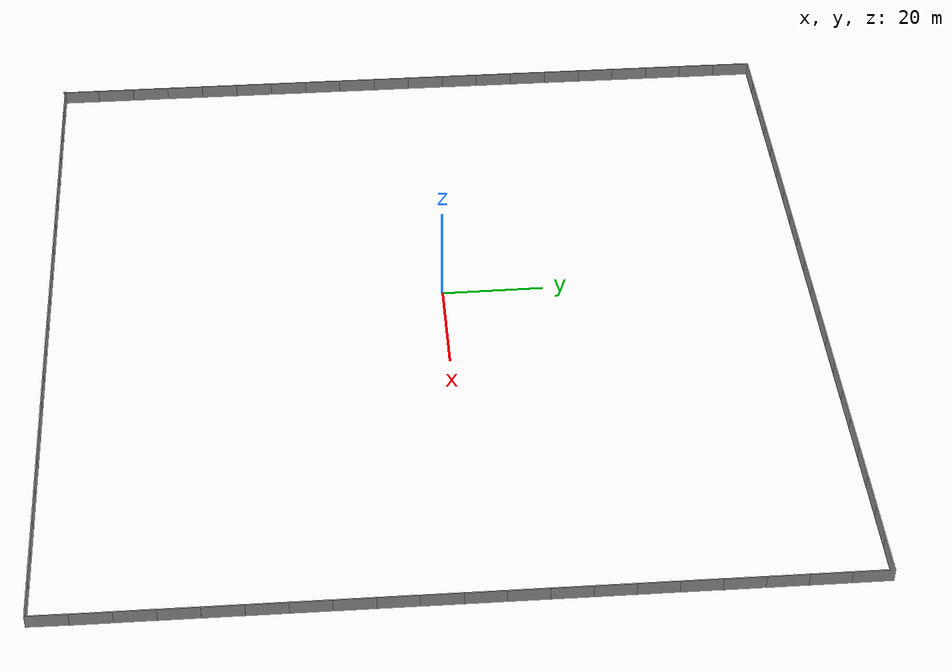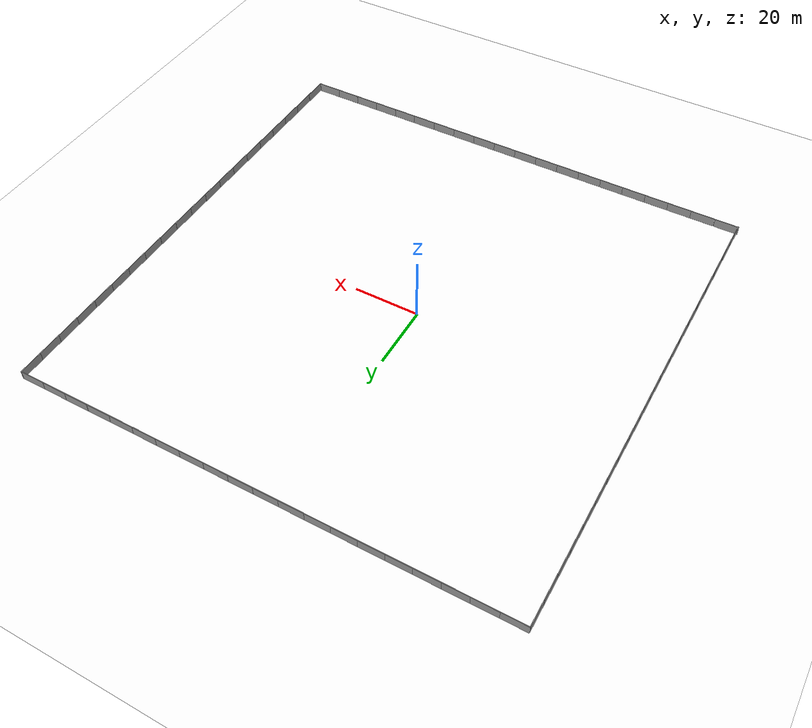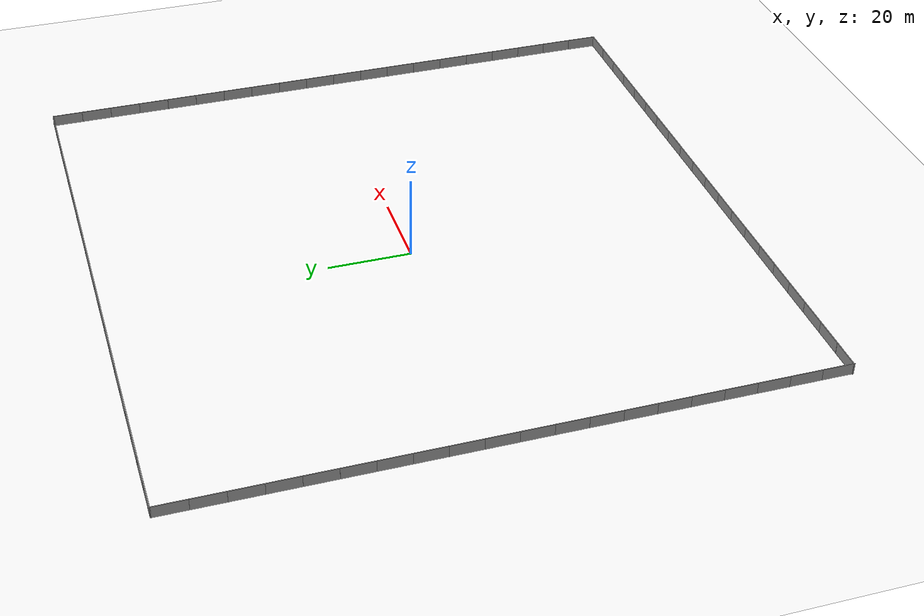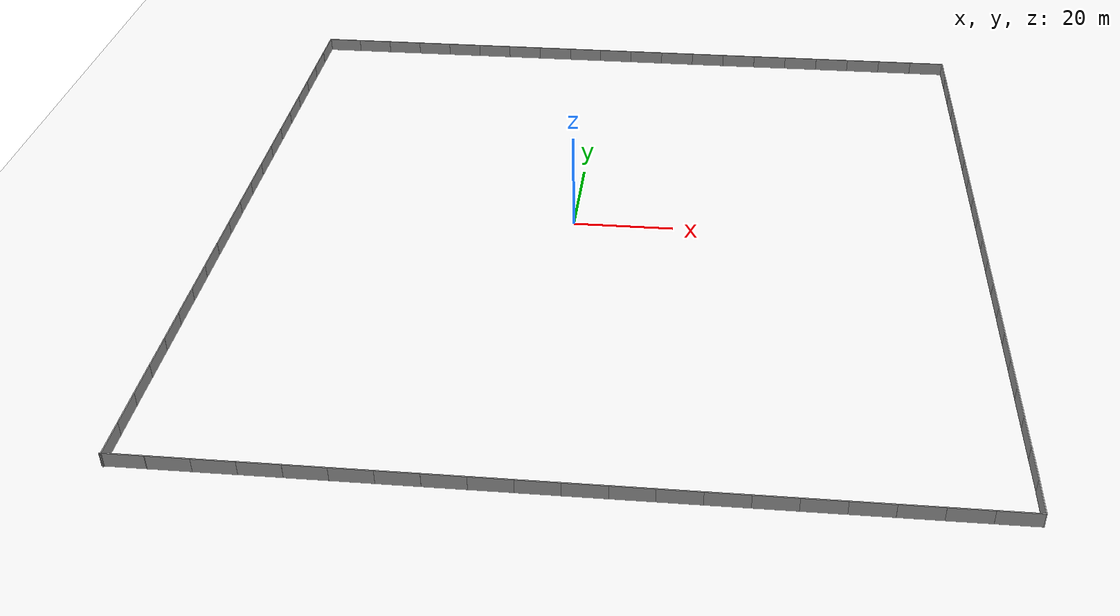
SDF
<sdf version="1.6">
 <world name="default">
  <plugin filename="gz-sim-physics-system" name="gz::sim::systems::Physics"/>
  <plugin filename="gz-sim-sensors-system" name="gz::sim::systems::Sensors">
   <render_engine>ogre2</render_engine>
  </plugin>
  <plugin filename="gz-sim-scene-broadcaster-system" name="gz::sim::systems::SceneBroadcaster"/>
  <plugin filename="gz-sim-user-commands-system" name="gz::sim::systems::UserCommands"/>
  <model name="grass_plane">
   <static>true</static>
   <link name="link">
    <collision name="collision">
     <geometry><plane><normal>0 0 1</normal><size>150 150</size></plane></geometry>
     <surface><friction><ode><mu>0.5</mu><mu2>.5</mu2></ode></friction></surface>
    </collision>
    <visual name="visual_s10">
     <cast_shadows>false</cast_shadows>
     <geometry>
      <plane><normal>0 0 1</normal><size>150 150</size></plane>
      <texture>
       <diffuse>materials/textures/Grass_Albedo.jpg</diffuse>
       <normal>materials/textures/flat_normal.png</normal>
       <size>10</size>
      </texture>
     </geometry>
     <material>
      <diffuse>1.0 1.0 1.0</diffuse>
      <specular>1.0 1.0 1.0</specular>
      <pbr>
       <metal>
        <albedo_map>model://forest/grass_plane/materials/textures/Grass_Albedo.jpg</albedo_map>
        <normal>model://forest/grass_plane/materials/textures/flat_normal.png</normal>
       </metal>
      </pbr>
     </material>
    </visual>
   </link>
   <pose>6.27224 -2.36963 0 0 -0 0</pose>
  </model>
  <model name="grey_wall_clone_10_clone_clone_clone_11_clone">
   <static>1</static>
   <link name="link">
    <pose>0 0 1.4 0 -0 0</pose>
    <collision name="collision"><geometry><box><size>7.5 0.2 2.8</size></box></geometry></collision>
    <visual name="visual">
     <cast_shadows>0</cast_shadows>
     <geometry><box><size>7.5 0.2 2.8</size></box></geometry>
     <material>
      <double_sided>true</double_sided>
      <diffuse>1.0 1.0 1.0</diffuse>
      <script>
       <uri>model://forest/grey_wall/materials/scripts</uri>
       <uri>model://forest/grey_wall/materials/textures</uri>
       <name>vrc/grey_wall</name>
      </script>
      <pbr><metal><albedo_map>model://forest/grey_wall/materials/textures/grey_wall.png</albedo_map></metal></pbr>
     </material>
    </visual>
   </link>
   <pose>-65.1256 -77.197 0 0 -0 0</pose>
  </model>
  <model name="grey_wall_clone_10_clone_clone_clone_11_clone_clone">
   <static>1</static>
   <link name="link">
    <pose>0 0 1.4 0 -0 0</pose>
    <collision name="collision"><geometry><box><size>7.5 0.2 2.8</size></box></geometry></collision>
    <visual name="visual">
     <cast_shadows>0</cast_shadows>
     <geometry><box><size>7.5 0.2 2.8</size></box></geometry>
     <material>
      <double_sided>true</double_sided>
      <diffuse>1.0 1.0 1.0</diffuse>
      <script>
       <uri>model://forest/grey_wall/materials/scripts</uri>
       <uri>model://forest/grey_wall/materials/textures</uri>
       <name>vrc/grey_wall</name>
      </script>
      <pbr><metal><albedo_map>model://forest/grey_wall/materials/textures/grey_wall.png</albedo_map></metal></pbr>
     </material>
    </visual>
   </link>
   <pose>-57.5346 -77.2024 0 0 -0 0</pose>
  </model>
  <model name="grey_wall_clone_10_clone_clone_clone_11_clone_clone_0">
   <static>1</static>
   <link name="link">
    <pose>0 0 1.4 0 -0 0</pose>
    <collision name="collision"><geometry><box><size>7.5 0.2 2.8</size></box></geometry></collision>
    <visual name="visual">
     <cast_shadows>0</cast_shadows>
     <geometry><box><size>7.5 0.2 2.8</size></box></geometry>
     <material>
      <double_sided>true</double_sided>
      <diffuse>1.0 1.0 1.0</diffuse>
      <script>
       <uri>model://forest/grey_wall/materials/scripts</uri>
       <uri>model://forest/grey_wall/materials/textures</uri>
       <name>vrc/grey_wall</name>
      </script>
      <pbr><metal><albedo_map>model://forest/grey_wall/materials/textures/grey_wall.png</albedo_map></metal></pbr>
     </material>
    </visual>
   </link>
   <pose>-50.026 -77.2083 0 0 -0 0</pose>
  </model>
  <model name="grey_wall_clone_10_clone_clone_clone_11_clone_clone_1">
   <static>1</static>
   <link name="link">
    <pose>0 0 1.4 0 -0 0</pose>
    <collision name="collision"><geometry><box><size>7.5 0.2 2.8</size></box></geometry></collision>
    <visual name="visual">
     <cast_shadows>0</cast_shadows>
     <geometry><box><size>7.5 0.2 2.8</size></box></geometry>
     <material>
      <double_sided>true</double_sided>
      <diffuse>1.0 1.0 1.0</diffuse>
      <script>
       <uri>model://forest/grey_wall/materials/scripts</uri>
       <uri>model://forest/grey_wall/materials/textures</uri>
       <name>vrc/grey_wall</name>
      </script>
      <pbr><metal><albedo_map>model://forest/grey_wall/materials/textures/grey_wall.png</albedo_map></metal></pbr>
     </material>
    </visual>
   </link>
   <pose>-42.5276 -77.1982 0 0 -0 0</pose>
  </model>
  <model name="grey_wall_clone_10_clone_clone_clone_11_clone_clone_2">
   <static>1</static>
   <link name="link">
    <pose>0 0 1.4 0 -0 0</pose>
    <collision name="collision"><geometry><box><size>7.5 0.2 2.8</size></box></geometry></collision>
    <visual name="visual">
     <cast_shadows>0</cast_shadows>
     <geometry><box><size>7.5 0.2 2.8</size></box></geometry>
     <material>
      <double_sided>true</double_sided>
      <diffuse>1.0 1.0 1.0</diffuse>
      <script>
       <uri>model://forest/grey_wall/materials/scripts</uri>
       <uri>model://forest/grey_wall/materials/textures</uri>
       <name>vrc/grey_wall</name>
      </script>
      <pbr><metal><albedo_map>model://forest/grey_wall/materials/textures/grey_wall.png</albedo_map></metal></pbr>
     </material>
    </visual>
   </link>
   <pose>-35.0175 -77.2078 0 0 -0 0</pose>
  </model>
  <model name="grey_wall_clone_10_clone_clone_clone_11_clone_clone_3">
   <static>1</static>
   <link name="link">
    <pose>0 0 1.4 0 -0 0</pose>
    <collision name="collision"><geometry><box><size>7.5 0.2 2.8</size></box></geometry></collision>
    <visual name="visual">
     <cast_shadows>0</cast_shadows>
     <geometry><box><size>7.5 0.2 2.8</size></box></geometry>
     <material>
      <double_sided>true</double_sided>
      <diffuse>1.0 1.0 1.0</diffuse>
      <script>
       <uri>model://forest/grey_wall/materials/scripts</uri>
       <uri>model://forest/grey_wall/materials/textures</uri>
       <name>vrc/grey_wall</name>
      </script>
      <pbr><metal><albedo_map>model://forest/grey_wall/materials/textures/grey_wall.png</albedo_map></metal></pbr>
     </material>
    </visual>
   </link>
   <pose>-27.5544 -77.2087 0 0 -0 0</pose>
  </model>
  <model name="grey_wall_clone_10_clone_clone_clone_11_clone_clone_4">
   <static>1</static>
   <link name="link">
    <pose>0 0 1.4 0 -0 0</pose>
    <collision name="collision"><geometry><box><size>7.5 0.2 2.8</size></box></geometry></collision>
    <visual name="visual">
     <cast_shadows>0</cast_shadows>
     <geometry><box><size>7.5 0.2 2.8</size></box></geometry>
     <material>
      <double_sided>true</double_sided>
      <diffuse>1.0 1.0 1.0</diffuse>
      <script>
       <uri>model://forest/grey_wall/materials/scripts</uri>
       <uri>model://forest/grey_wall/materials/textures</uri>
       <name>vrc/grey_wall</name>
      </script>
      <pbr><metal><albedo_map>model://forest/grey_wall/materials/textures/grey_wall.png</albedo_map></metal></pbr>
     </material>
    </visual>
   </link>
   <pose>-20.0557 -77.2142 0 0 -0 0</pose>
  </model>
  <model name="grey_wall_clone_10_clone_clone_clone_11_clone_clone_5">
   <static>1</static>
   <link name="link">
    <pose>0 0 1.4 0 -0 0</pose>
    <collision name="collision"><geometry><box><size>7.5 0.2 2.8</size></box></geometry></collision>
    <visual name="visual">
     <cast_shadows>0</cast_shadows>
     <geometry><box><size>7.5 0.2 2.8</size></box></geometry>
     <material>
      <double_sided>true</double_sided>
      <diffuse>1.0 1.0 1.0</diffuse>
      <script>
       <uri>model://forest/grey_wall/materials/scripts</uri>
       <uri>model://forest/grey_wall/materials/textures</uri>
       <name>vrc/grey_wall</name>
      </script>
      <pbr><metal><albedo_map>model://forest/grey_wall/materials/textures/grey_wall.png</albedo_map></metal></pbr>
     </material>
    </visual>
   </link>
   <pose>-12.5467 -77.224 0 0 -0 0</pose>
  </model>
  <model name="grey_wall_clone_10_clone_clone_clone_11_clone_clone_6">
   <static>1</static>
   <link name="link">
    <pose>0 0 1.4 0 -0 0</pose>
    <collision name="collision"><geometry><box><size>7.5 0.2 2.8</size></box></geometry></collision>
    <visual name="visual">
     <cast_shadows>0</cast_shadows>
     <geometry><box><size>7.5 0.2 2.8</size></box></geometry>
     <material>
      <double_sided>true</double_sided>
      <diffuse>1.0 1.0 1.0</diffuse>
      <script>
       <uri>model://forest/grey_wall/materials/scripts</uri>
       <uri>model://forest/grey_wall/materials/textures</uri>
       <name>vrc/grey_wall</name>
      </script>
      <pbr><metal><albedo_map>model://forest/grey_wall/materials/textures/grey_wall.png</albedo_map></metal></pbr>
     </material>
    </visual>
   </link>
   <pose>-5.04952 -77.2253 0 0 -0 0</pose>
  </model>
  <model name="grey_wall_clone_10_clone_clone_clone_11_clone_clone_7">
   <static>1</static>
   <link name="link">
    <pose>0 0 1.4 0 -0 0</pose>
    <collision name="collision"><geometry><box><size>7.5 0.2 2.8</size></box></geometry></collision>
    <visual name="visual">
     <cast_shadows>0</cast_shadows>
     <geometry><box><size>7.5 0.2 2.8</size></box></geometry>
     <material>
      <double_sided>true</double_sided>
      <diffuse>1.0 1.0 1.0</diffuse>
      <script>
       <uri>model://forest/grey_wall/materials/scripts</uri>
       <uri>model://forest/grey_wall/materials/textures</uri>
       <name>vrc/grey_wall</name>
      </script>
      <pbr><metal><albedo_map>model://forest/grey_wall/materials/textures/grey_wall.png</albedo_map></metal></pbr>
     </material>
    </visual>
   </link>
   <pose>2.45064 -77.2385 0 0 -0 0</pose>
  </model>
  <model name="grey_wall_clone_10_clone_clone_clone_11_clone_clone_8">
   <static>1</static>
   <link name="link">
    <pose>0 0 1.4 0 -0 0</pose>
    <collision name="collision"><geometry><box><size>7.5 0.2 2.8</size></box></geometry></collision>
    <visual name="visual">
     <cast_shadows>0</cast_shadows>
     <geometry><box><size>7.5 0.2 2.8</size></box></geometry>
     <material>
      <double_sided>true</double_sided>
      <diffuse>1.0 1.0 1.0</diffuse>
      <script>
       <uri>model://forest/grey_wall/materials/scripts</uri>
       <uri>model://forest/grey_wall/materials/textures</uri>
       <name>vrc/grey_wall</name>
      </script>
      <pbr><metal><albedo_map>model://forest/grey_wall/materials/textures/grey_wall.png</albedo_map></metal></pbr>
     </material>
    </visual>
   </link>
   <pose>9.9578 -77.2456 0 0 -0 0</pose>
  </model>
  <model name="grey_wall_clone_10_clone_clone_clone_11_clone_clone_9">
   <static>1</static>
   <link name="link">
    <pose>0 0 1.4 0 -0 0</pose>
    <collision name="collision"><geometry><box><size>7.5 0.2 2.8</size></box></geometry></collision>
    <visual name="visual">
     <cast_shadows>0</cast_shadows>
     <geometry><box><size>7.5 0.2 2.8</size></box></geometry>
     <material>
      <double_sided>true</double_sided>
      <diffuse>1.0 1.0 1.0</diffuse>
      <script>
       <uri>model://forest/grey_wall/materials/scripts</uri>
       <uri>model://forest/grey_wall/materials/textures</uri>
       <name>vrc/grey_wall</name>
      </script>
      <pbr><metal><albedo_map>model://forest/grey_wall/materials/textures/grey_wall.png</albedo_map></metal></pbr>
     </material>
    </visual>
   </link>
   <pose>17.442 -77.2428 0 0 -0 0</pose>
  </model>
  <model name="grey_wall_clone_10_clone_clone_clone_11_clone_clone_10">
   <static>1</static>
   <link name="link">
    <pose>0 0 1.4 0 -0 0</pose>
    <collision name="collision"><geometry><box><size>7.5 0.2 2.8</size></box></geometry></collision>
    <visual name="visual">
     <cast_shadows>0</cast_shadows>
     <geometry><box><size>7.5 0.2 2.8</size></box></geometry>
     <material>
      <double_sided>true</double_sided>
      <diffuse>1.0 1.0 1.0</diffuse>
      <script>
       <uri>model://forest/grey_wall/materials/scripts</uri>
       <uri>model://forest/grey_wall/materials/textures</uri>
       <name>vrc/grey_wall</name>
      </script>
      <pbr><metal><albedo_map>model://forest/grey_wall/materials/textures/grey_wall.png</albedo_map></metal></pbr>
     </material>
    </visual>
   </link>
   <pose>24.9441 -77.2473 0 0 -0 0</pose>
  </model>
  <model name="grey_wall_clone_10_clone_clone_clone_11_clone_clone_11">
   <static>1</static>
   <link name="link">
    <pose>0 0 1.4 0 -0 0</pose>
    <collision name="collision"><geometry><box><size>7.5 0.2 2.8</size></box></geometry></collision>
    <visual name="visual">
     <cast_shadows>0</cast_shadows>
     <geometry><box><size>7.5 0.2 2.8</size></box></geometry>
     <material>
      <double_sided>true</double_sided>
      <diffuse>1.0 1.0 1.0</diffuse>
      <script>
       <uri>model://forest/grey_wall/materials/scripts</uri>
       <uri>model://forest/grey_wall/materials/textures</uri>
       <name>vrc/grey_wall</name>
      </script>
      <pbr><metal><albedo_map>model://forest/grey_wall/materials/textures/grey_wall.png</albedo_map></metal></pbr>
     </material>
    </visual>
   </link>
   <pose>32.4421 -77.2463 0 0 -0 0</pose>
  </model>
  <model name="grey_wall_clone_10_clone_clone_clone_11_clone_clone_12">
   <static>1</static>
   <link name="link">
    <pose>0 0 1.4 0 -0 0</pose>
    <collision name="collision"><geometry><box><size>7.5 0.2 2.8</size></box></geometry></collision>
    <visual name="visual">
     <cast_shadows>0</cast_shadows>
     <geometry><box><size>7.5 0.2 2.8</size></box></geometry>
     <material>
      <double_sided>true</double_sided>
      <diffuse>1.0 1.0 1.0</diffuse>
      <script>
       <uri>model://forest/grey_wall/materials/scripts</uri>
       <uri>model://forest/grey_wall/materials/textures</uri>
       <name>vrc/grey_wall</name>
      </script>
      <pbr><metal><albedo_map>model://forest/grey_wall/materials/textures/grey_wall.png</albedo_map></metal></pbr>
     </material>
    </visual>
   </link>
   <pose>39.9314 -77.2456 0 0 -0 0</pose>
  </model>
  <model name="grey_wall_clone_10_clone_clone_clone_11_clone_clone_13">
   <static>1</static>
   <link name="link">
    <pose>0 0 1.4 0 -0 0</pose>
    <collision name="collision"><geometry><box><size>7.5 0.2 2.8</size></box></geometry></collision>
    <visual name="visual">
     <cast_shadows>0</cast_shadows>
     <geometry><box><size>7.5 0.2 2.8</size></box></geometry>
     <material>
      <double_sided>true</double_sided>
      <diffuse>1.0 1.0 1.0</diffuse>
      <script>
       <uri>model://forest/grey_wall/materials/scripts</uri>
       <uri>model://forest/grey_wall/materials/textures</uri>
       <name>vrc/grey_wall</name>
      </script>
      <pbr><metal><albedo_map>model://forest/grey_wall/materials/textures/grey_wall.png</albedo_map></metal></pbr>
     </material>
    </visual>
   </link>
   <pose>47.429 -77.2489 0 0 -0 0</pose>
  </model>
  <model name="grey_wall_clone_10_clone_clone_clone_11_clone_clone_14">
   <static>1</static>
   <link name="link">
    <pose>0 0 1.4 0 -0 0</pose>
    <collision name="collision"><geometry><box><size>7.5 0.2 2.8</size></box></geometry></collision>
    <visual name="visual">
     <cast_shadows>0</cast_shadows>
     <geometry><box><size>7.5 0.2 2.8</size></box></geometry>
     <material>
      <double_sided>true</double_sided>
      <diffuse>1.0 1.0 1.0</diffuse>
      <script>
       <uri>model://forest/grey_wall/materials/scripts</uri>
       <uri>model://forest/grey_wall/materials/textures</uri>
       <name>vrc/grey_wall</name>
      </script>
      <pbr><metal><albedo_map>model://forest/grey_wall/materials/textures/grey_wall.png</albedo_map></metal></pbr>
     </material>
    </visual>
   </link>
   <pose>54.8935 -77.2438 0 0 -0 0</pose>
  </model>
  <model name="grey_wall_clone_10_clone_clone_clone_11_clone_clone_15">
   <static>1</static>
   <link name="link">
    <pose>0 0 1.4 0 -0 0</pose>
    <collision name="collision"><geometry><box><size>7.5 0.2 2.8</size></box></geometry></collision>
    <visual name="visual">
     <cast_shadows>0</cast_shadows>
     <geometry><box><size>7.5 0.2 2.8</size></box></geometry>
     <material>
      <double_sided>true</double_sided>
      <diffuse>1.0 1.0 1.0</diffuse>
      <script>
       <uri>model://forest/grey_wall/materials/scripts</uri>
       <uri>model://forest/grey_wall/materials/textures</uri>
       <name>vrc/grey_wall</name>
      </script>
      <pbr><metal><albedo_map>model://forest/grey_wall/materials/textures/grey_wall.png</albedo_map></metal></pbr>
     </material>
    </visual>
   </link>
   <pose>62.4043 -77.2429 0 0 -0 0</pose>
  </model>
  <model name="grey_wall_clone_10_clone_clone_clone_11_clone_clone_16">
   <static>1</static>
   <link name="link">
    <pose>0 0 1.4 0 -0 0</pose>
    <collision name="collision"><geometry><box><size>7.5 0.2 2.8</size></box></geometry></collision>
    <visual name="visual">
     <cast_shadows>0</cast_shadows>
     <geometry><box><size>7.5 0.2 2.8</size></box></geometry>
     <material>
      <double_sided>true</double_sided>
      <diffuse>1.0 1.0 1.0</diffuse>
      <script>
       <uri>model://forest/grey_wall/materials/scripts</uri>
       <uri>model://forest/grey_wall/materials/textures</uri>
       <name>vrc/grey_wall</name>
      </script>
      <pbr><metal><albedo_map>model://forest/grey_wall/materials/textures/grey_wall.png</albedo_map></metal></pbr>
     </material>
    </visual>
   </link>
   <pose>69.8968 -77.2494 0 0 -0 0</pose>
  </model>
  <model name="grey_wall_clone_10_clone_clone_clone_11_clone_clone_17">
   <static>1</static>
   <link name="link">
    <pose>0 0 1.4 0 -0 0</pose>
    <collision name="collision"><geometry><box><size>7.5 0.2 2.8</size></box></geometry></collision>
    <visual name="visual">
     <cast_shadows>0</cast_shadows>
     <geometry><box><size>7.5 0.2 2.8</size></box></geometry>
     <material>
      <double_sided>true</double_sided>
      <diffuse>1.0 1.0 1.0</diffuse>
      <script>
       <uri>model://forest/grey_wall/materials/scripts</uri>
       <uri>model://forest/grey_wall/materials/textures</uri>
       <name>vrc/grey_wall</name>
      </script>
      <pbr><metal><albedo_map>model://forest/grey_wall/materials/textures/grey_wall.png</albedo_map></metal></pbr>
     </material>
    </visual>
   </link>
   <pose>77.4066 -77.2521 0 0 -0 0</pose>
  </model>
  <model name="grey_wall_clone_10_clone_0_clone_11_clone">
   <static>1</static>
   <link name="link">
    <pose>0 0 1.4 0 -0 0</pose>
    <collision name="collision"><geometry><box><size>7.5 0.2 2.8</size></box></geometry></collision>
    <visual name="visual">
     <cast_shadows>0</cast_shadows>
     <geometry><box><size>7.5 0.2 2.8</size></box></geometry>
     <material>
      <double_sided>true</double_sided>
      <diffuse>1.0 1.0 1.0</diffuse>
      <script>
       <uri>model://forest/grey_wall/materials/scripts</uri>
       <uri>model://forest/grey_wall/materials/textures</uri>
       <name>vrc/grey_wall</name>
      </script>
      <pbr><metal><albedo_map>model://forest/grey_wall/materials/textures/grey_wall.png</albedo_map></metal></pbr>
     </material>
    </visual>
   </link>
   <pose>81.2442 -73.5802 0 0 0 -1.5802</pose>
  </model>
  <model name="grey_wall_clone_10_clone_0_clone_10_clone">
   <static>1</static>
   <link name="link">
    <pose>0 0 1.4 0 -0 0</pose>
    <collision name="collision"><geometry><box><size>7.5 0.2 2.8</size></box></geometry></collision>
    <visual name="visual">
     <cast_shadows>0</cast_shadows>
     <geometry><box><size>7.5 0.2 2.8</size></box></geometry>
     <material>
      <double_sided>true</double_sided>
      <diffuse>1.0 1.0 1.0</diffuse>
      <script>
       <uri>model://forest/grey_wall/materials/scripts</uri>
       <uri>model://forest/grey_wall/materials/textures</uri>
       <name>vrc/grey_wall</name>
      </script>
      <pbr><metal><albedo_map>model://forest/grey_wall/materials/textures/grey_wall.png</albedo_map></metal></pbr>
     </material>
    </visual>
   </link>
   <pose>81.3001 -66.0858 0 0 0 -1.56932</pose>
  </model>
  <model name="grey_wall_clone_10_clone_0_clone_9_clone">
   <static>1</static>
   <link name="link">
    <pose>0 0 1.4 0 -0 0</pose>
    <collision name="collision"><geometry><box><size>7.5 0.2 2.8</size></box></geometry></collision>
    <visual name="visual">
     <cast_shadows>0</cast_shadows>
     <geometry><box><size>7.5 0.2 2.8</size></box></geometry>
     <material>
      <double_sided>true</double_sided>
      <diffuse>1.0 1.0 1.0</diffuse>
      <script>
       <uri>model://forest/grey_wall/materials/scripts</uri>
       <uri>model://forest/grey_wall/materials/textures</uri>
       <name>vrc/grey_wall</name>
      </script>
      <pbr><metal><albedo_map>model://forest/grey_wall/materials/textures/grey_wall.png</albedo_map></metal></pbr>
     </material>
    </visual>
   </link>
   <pose>81.2777 -58.6142 0 0 0 -1.56932</pose>
  </model>
  <model name="grey_wall_clone_10_clone_0_clone_8_clone">
   <static>1</static>
   <link name="link">
    <pose>0 0 1.4 0 -0 0</pose>
    <collision name="collision"><geometry><box><size>7.5 0.2 2.8</size></box></geometry></collision>
    <visual name="visual">
     <cast_shadows>0</cast_shadows>
     <geometry><box><size>7.5 0.2 2.8</size></box></geometry>
     <material>
      <double_sided>true</double_sided>
      <diffuse>1.0 1.0 1.0</diffuse>
      <script>
       <uri>model://forest/grey_wall/materials/scripts</uri>
       <uri>model://forest/grey_wall/materials/textures</uri>
       <name>vrc/grey_wall</name>
      </script>
      <pbr><metal><albedo_map>model://forest/grey_wall/materials/textures/grey_wall.png</albedo_map></metal></pbr>
     </material>
    </visual>
   </link>
   <pose>81.2777 -51.1177 0 0 0 -1.56932</pose>
  </model>
  <model name="grey_wall_clone_10_clone_0_clone_7_clone">
   <static>1</static>
   <link name="link">
    <pose>0 0 1.4 0 -0 0</pose>
    <collision name="collision"><geometry><box><size>7.5 0.2 2.8</size></box></geometry></collision>
    <visual name="visual">
     <cast_shadows>0</cast_shadows>
     <geometry><box><size>7.5 0.2 2.8</size></box></geometry>
     <material>
      <double_sided>true</double_sided>
      <diffuse>1.0 1.0 1.0</diffuse>
      <script>
       <uri>model://forest/grey_wall/materials/scripts</uri>
       <uri>model://forest/grey_wall/materials/textures</uri>
       <name>vrc/grey_wall</name>
      </script>
      <pbr><metal><albedo_map>model://forest/grey_wall/materials/textures/grey_wall.png</albedo_map></metal></pbr>
     </material>
    </visual>
   </link>
   <pose>81.2788 -43.6064 0 0 0 -1.56932</pose>
  </model>
  <model name="grey_wall_clone_10_clone_0_clone_6_clone">
   <static>1</static>
   <link name="link">
    <pose>0 0 1.4 0 -0 0</pose>
    <collision name="collision"><geometry><box><size>7.5 0.2 2.8</size></box></geometry></collision>
    <visual name="visual">
     <cast_shadows>0</cast_shadows>
     <geometry><box><size>7.5 0.2 2.8</size></box></geometry>
     <material>
      <double_sided>true</double_sided>
      <diffuse>1.0 1.0 1.0</diffuse>
      <script>
       <uri>model://forest/grey_wall/materials/scripts</uri>
       <uri>model://forest/grey_wall/materials/textures</uri>
       <name>vrc/grey_wall</name>
      </script>
      <pbr><metal><albedo_map>model://forest/grey_wall/materials/textures/grey_wall.png</albedo_map></metal></pbr>
     </material>
    </visual>
   </link>
   <pose>81.2767 -36.0958 0 0 0 -1.56932</pose>
  </model>
  <model name="grey_wall_clone_10_clone_0_clone_5_clone_13">
   <static>1</static>
   <link name="link">
    <pose>0 0 1.4 0 -0 0</pose>
    <collision name="collision"><geometry><box><size>7.5 0.2 2.8</size></box></geometry></collision>
    <visual name="visual">
     <cast_shadows>0</cast_shadows>
     <geometry><box><size>7.5 0.2 2.8</size></box></geometry>
     <material>
      <double_sided>true</double_sided>
      <diffuse>1.0 1.0 1.0</diffuse>
      <script>
       <uri>model://forest/grey_wall/materials/scripts</uri>
       <uri>model://forest/grey_wall/materials/textures</uri>
       <name>vrc/grey_wall</name>
      </script>
      <pbr><metal><albedo_map>model://forest/grey_wall/materials/textures/grey_wall.png</albedo_map></metal></pbr>
     </material>
    </visual>
   </link>
   <pose>81.2728 -28.5811 0 0 0 -1.56932</pose>
  </model>
  <model name="grey_wall_clone_10_clone_0_clone_4_clone">
   <static>1</static>
   <link name="link">
    <pose>0 0 1.4 0 -0 0</pose>
    <collision name="collision"><geometry><box><size>7.5 0.2 2.8</size></box></geometry></collision>
    <visual name="visual">
     <cast_shadows>0</cast_shadows>
     <geometry><box><size>7.5 0.2 2.8</size></box></geometry>
     <material>
      <double_sided>true</double_sided>
      <diffuse>1.0 1.0 1.0</diffuse>
      <script>
       <uri>model://forest/grey_wall/materials/scripts</uri>
       <uri>model://forest/grey_wall/materials/textures</uri>
       <name>vrc/grey_wall</name>
      </script>
      <pbr><metal><albedo_map>model://forest/grey_wall/materials/textures/grey_wall.png</albedo_map></metal></pbr>
     </material>
    </visual>
   </link>
   <pose>81.2736 -21.0806 0 0 0 -1.56932</pose>
  </model>
  <model name="grey_wall_clone_10_clone_0_clone_3_clone">
   <static>1</static>
   <link name="link">
    <pose>0 0 1.4 0 -0 0</pose>
    <collision name="collision"><geometry><box><size>7.5 0.2 2.8</size></box></geometry></collision>
    <visual name="visual">
     <cast_shadows>0</cast_shadows>
     <geometry><box><size>7.5 0.2 2.8</size></box></geometry>
     <material>
      <double_sided>true</double_sided>
      <diffuse>1.0 1.0 1.0</diffuse>
      <script>
       <uri>model://forest/grey_wall/materials/scripts</uri>
       <uri>model://forest/grey_wall/materials/textures</uri>
       <name>vrc/grey_wall</name>
      </script>
      <pbr><metal><albedo_map>model://forest/grey_wall/materials/textures/grey_wall.png</albedo_map></metal></pbr>
     </material>
    </visual>
   </link>
   <pose>81.2554 -13.5842 0 0 0 -1.56932</pose>
  </model>
  <model name="grey_wall_clone_10_clone_0_clone_2_clone">
   <static>1</static>
   <link name="link">
    <pose>0 0 1.4 0 -0 0</pose>
    <collision name="collision"><geometry><box><size>7.5 0.2 2.8</size></box></geometry></collision>
    <visual name="visual">
     <cast_shadows>0</cast_shadows>
     <geometry><box><size>7.5 0.2 2.8</size></box></geometry>
     <material>
      <double_sided>true</double_sided>
      <diffuse>1.0 1.0 1.0</diffuse>
      <script>
       <uri>model://forest/grey_wall/materials/scripts</uri>
       <uri>model://forest/grey_wall/materials/textures</uri>
       <name>vrc/grey_wall</name>
      </script>
      <pbr><metal><albedo_map>model://forest/grey_wall/materials/textures/grey_wall.png</albedo_map></metal></pbr>
     </material>
    </visual>
   </link>
   <pose>81.262 -6.06923 0 0 0 -1.56932</pose>
  </model>
  <model name="grey_wall_clone_10_clone_0_clone_1_clone">
   <static>1</static>
   <link name="link">
    <pose>0 0 1.4 0 -0 0</pose>
    <collision name="collision"><geometry><box><size>7.5 0.2 2.8</size></box></geometry></collision>
    <visual name="visual">
     <cast_shadows>0</cast_shadows>
     <geometry><box><size>7.5 0.2 2.8</size></box></geometry>
     <material>
      <double_sided>true</double_sided>
      <diffuse>1.0 1.0 1.0</diffuse>
      <script>
       <uri>model://forest/grey_wall/materials/scripts</uri>
       <uri>model://forest/grey_wall/materials/textures</uri>
       <name>vrc/grey_wall</name>
      </script>
      <pbr><metal><albedo_map>model://forest/grey_wall/materials/textures/grey_wall.png</albedo_map></metal></pbr>
     </material>
    </visual>
   </link>
   <pose>81.2538 1.43804 0 0 0 -1.56932</pose>
  </model>
  <model name="grey_wall_clone_10_clone_0_clone_0_clone">
   <static>1</static>
   <link name="link">
    <pose>0 0 1.4 0 -0 0</pose>
    <collision name="collision"><geometry><box><size>7.5 0.2 2.8</size></box></geometry></collision>
    <visual name="visual">
     <cast_shadows>0</cast_shadows>
     <geometry><box><size>7.5 0.2 2.8</size></box></geometry>
     <material>
      <double_sided>true</double_sided>
      <diffuse>1.0 1.0 1.0</diffuse>
      <script>
       <uri>model://forest/grey_wall/materials/scripts</uri>
       <uri>model://forest/grey_wall/materials/textures</uri>
       <name>vrc/grey_wall</name>
      </script>
      <pbr><metal><albedo_map>model://forest/grey_wall/materials/textures/grey_wall.png</albedo_map></metal></pbr>
     </material>
    </visual>
   </link>
   <pose>81.2487 8.94341 0 0 0 -1.56932</pose>
  </model>
  <model name="grey_wall_clone_10_clone_0_clone_clone">
   <static>1</static>
   <link name="link">
    <pose>0 0 1.4 0 -0 0</pose>
    <collision name="collision"><geometry><box><size>7.5 0.2 2.8</size></box></geometry></collision>
    <visual name="visual">
     <cast_shadows>0</cast_shadows>
     <geometry><box><size>7.5 0.2 2.8</size></box></geometry>
     <material>
      <double_sided>true</double_sided>
      <diffuse>1.0 1.0 1.0</diffuse>
      <script>
       <uri>model://forest/grey_wall/materials/scripts</uri>
       <uri>model://forest/grey_wall/materials/textures</uri>
       <name>vrc/grey_wall</name>
      </script>
      <pbr><metal><albedo_map>model://forest/grey_wall/materials/textures/grey_wall.png</albedo_map></metal></pbr>
     </material>
    </visual>
   </link>
   <pose>81.244 16.4592 0 0 0 -1.56932</pose>
  </model>
  <model name="grey_wall_clone_10_clone_0_clone_12">
   <static>1</static>
   <link name="link">
    <pose>0 0 1.4 0 -0 0</pose>
    <collision name="collision"><geometry><box><size>7.5 0.2 2.8</size></box></geometry></collision>
    <visual name="visual">
     <cast_shadows>0</cast_shadows>
     <geometry><box><size>7.5 0.2 2.8</size></box></geometry>
     <material>
      <double_sided>true</double_sided>
      <diffuse>1.0 1.0 1.0</diffuse>
      <script>
       <uri>model://forest/grey_wall/materials/scripts</uri>
       <uri>model://forest/grey_wall/materials/textures</uri>
       <name>vrc/grey_wall</name>
      </script>
      <pbr><metal><albedo_map>model://forest/grey_wall/materials/textures/grey_wall.png</albedo_map></metal></pbr>
     </material>
    </visual>
   </link>
   <pose>81.241 23.9604 0 0 0 -1.56932</pose>
  </model>
  <model name="grey_wall_clone_10_clone_0_clone_13">
   <static>1</static>
   <link name="link">
    <pose>0 0 1.4 0 -0 0</pose>
    <collision name="collision"><geometry><box><size>7.5 0.2 2.8</size></box></geometry></collision>
    <visual name="visual">
     <cast_shadows>0</cast_shadows>
     <geometry><box><size>7.5 0.2 2.8</size></box></geometry>
     <material>
      <double_sided>true</double_sided>
      <diffuse>1.0 1.0 1.0</diffuse>
      <script>
       <uri>model://forest/grey_wall/materials/scripts</uri>
       <uri>model://forest/grey_wall/materials/textures</uri>
       <name>vrc/grey_wall</name>
      </script>
      <pbr><metal><albedo_map>model://forest/grey_wall/materials/textures/grey_wall.png</albedo_map></metal></pbr>
     </material>
    </visual>
   </link>
   <pose>81.233 31.4667 0 0 0 -1.56932</pose>
  </model>
  <model name="grey_wall_clone_10_clone_0_clone_14">
   <static>1</static>
   <link name="link">
    <pose>0 0 1.4 0 -0 0</pose>
    <collision name="collision"><geometry><box><size>7.5 0.2 2.8</size></box></geometry></collision>
    <visual name="visual">
     <cast_shadows>0</cast_shadows>
     <geometry><box><size>7.5 0.2 2.8</size></box></geometry>
     <material>
      <double_sided>true</double_sided>
      <diffuse>1.0 1.0 1.0</diffuse>
      <script>
       <uri>model://forest/grey_wall/materials/scripts</uri>
       <uri>model://forest/grey_wall/materials/textures</uri>
       <name>vrc/grey_wall</name>
      </script>
      <pbr><metal><albedo_map>model://forest/grey_wall/materials/textures/grey_wall.png</albedo_map></metal></pbr>
     </material>
    </visual>
   </link>
   <pose>81.2299 38.978 0 0 0 -1.56932</pose>
  </model>
  <model name="grey_wall_clone_10_clone_0_clone_15">
   <static>1</static>
   <link name="link">
    <pose>0 0 1.4 0 -0 0</pose>
    <collision name="collision"><geometry><box><size>7.5 0.2 2.8</size></box></geometry></collision>
    <visual name="visual">
     <cast_shadows>0</cast_shadows>
     <geometry><box><size>7.5 0.2 2.8</size></box></geometry>
     <material>
      <double_sided>true</double_sided>
      <diffuse>1.0 1.0 1.0</diffuse>
      <script>
       <uri>model://forest/grey_wall/materials/scripts</uri>
       <uri>model://forest/grey_wall/materials/textures</uri>
       <name>vrc/grey_wall</name>
      </script>
      <pbr><metal><albedo_map>model://forest/grey_wall/materials/textures/grey_wall.png</albedo_map></metal></pbr>
     </material>
    </visual>
   </link>
   <pose>81.2399 46.4861 0 0 0 -1.56932</pose>
  </model>
  <model name="grey_wall_clone_10_clone_0_clone_16">
   <static>1</static>
   <link name="link">
    <pose>0 0 1.4 0 -0 0</pose>
    <collision name="collision"><geometry><box><size>7.5 0.2 2.8</size></box></geometry></collision>
    <visual name="visual">
     <cast_shadows>0</cast_shadows>
     <geometry><box><size>7.5 0.2 2.8</size></box></geometry>
     <material>
      <double_sided>true</double_sided>
      <diffuse>1.0 1.0 1.0</diffuse>
      <script>
       <uri>model://forest/grey_wall/materials/scripts</uri>
       <uri>model://forest/grey_wall/materials/textures</uri>
       <name>vrc/grey_wall</name>
      </script>
      <pbr><metal><albedo_map>model://forest/grey_wall/materials/textures/grey_wall.png</albedo_map></metal></pbr>
     </material>
    </visual>
   </link>
   <pose>81.2341 53.9889 0 0 0 -1.56932</pose>
  </model>
  <model name="grey_wall_clone_10_clone_0_clone_17">
   <static>1</static>
   <link name="link">
    <pose>0 0 1.4 0 -0 0</pose>
    <collision name="collision"><geometry><box><size>7.5 0.2 2.8</size></box></geometry></collision>
    <visual name="visual">
     <cast_shadows>0</cast_shadows>
     <geometry><box><size>7.5 0.2 2.8</size></box></geometry>
     <material>
      <double_sided>true</double_sided>
      <diffuse>1.0 1.0 1.0</diffuse>
      <script>
       <uri>model://forest/grey_wall/materials/scripts</uri>
       <uri>model://forest/grey_wall/materials/textures</uri>
       <name>vrc/grey_wall</name>
      </script>
      <pbr><metal><albedo_map>model://forest/grey_wall/materials/textures/grey_wall.png</albedo_map></metal></pbr>
     </material>
    </visual>
   </link>
   <pose>81.2319 61.4946 0 0 0 -1.56932</pose>
  </model>
  <model name="grey_wall_clone_10_clone_0_clone_18">
   <static>1</static>
   <link name="link">
    <pose>0 0 1.4 0 -0 0</pose>
    <collision name="collision"><geometry><box><size>7.5 0.2 2.8</size></box></geometry></collision>
    <visual name="visual">
     <cast_shadows>0</cast_shadows>
     <geometry><box><size>7.5 0.2 2.8</size></box></geometry>
     <material>
      <double_sided>true</double_sided>
      <diffuse>1.0 1.0 1.0</diffuse>
      <script>
       <uri>model://forest/grey_wall/materials/scripts</uri>
       <uri>model://forest/grey_wall/materials/textures</uri>
       <name>vrc/grey_wall</name>
      </script>
      <pbr><metal><albedo_map>model://forest/grey_wall/materials/textures/grey_wall.png</albedo_map></metal></pbr>
     </material>
    </visual>
   </link>
   <pose>81.2148 68.9647 0 0 0 -1.56932</pose>
  </model>
  <model name="grey_wall_clone_10_clone_clone_0">
   <static>1</static>
   <link name="link">
    <pose>0 0 1.4 0 -0 0</pose>
    <collision name="collision"><geometry><box><size>7.5 0.2 2.8</size></box></geometry></collision>
    <visual name="visual">
     <cast_shadows>0</cast_shadows>
     <geometry><box><size>7.5 0.2 2.8</size></box></geometry>
     <material>
      <double_sided>true</double_sided>
      <diffuse>1.0 1.0 1.0</diffuse>
      <script>
       <uri>model://forest/grey_wall/materials/scripts</uri>
       <uri>model://forest/grey_wall/materials/textures</uri>
       <name>vrc/grey_wall</name>
      </script>
      <pbr><metal><albedo_map>model://forest/grey_wall/materials/textures/grey_wall.png</albedo_map></metal></pbr>
     </material>
    </visual>
   </link>
   <pose>77.3508 72.6116 0 0 -0 0</pose>
  </model>
  <model name="grey_wall_clone_10_clone_clone_1">
   <static>1</static>
   <link name="link">
    <pose>0 0 1.4 0 -0 0</pose>
    <collision name="collision"><geometry><box><size>7.5 0.2 2.8</size></box></geometry></collision>
    <visual name="visual">
     <cast_shadows>0</cast_shadows>
     <geometry><box><size>7.5 0.2 2.8</size></box></geometry>
     <material>
      <double_sided>true</double_sided>
      <diffuse>1.0 1.0 1.0</diffuse>
      <script>
       <uri>model://forest/grey_wall/materials/scripts</uri>
       <uri>model://forest/grey_wall/materials/textures</uri>
       <name>vrc/grey_wall</name>
      </script>
      <pbr><metal><albedo_map>model://forest/grey_wall/materials/textures/grey_wall.png</albedo_map></metal></pbr>
     </material>
    </visual>
   </link>
   <pose>69.8438 72.6289 0 0 -0 0</pose>
  </model>
  <model name="grey_wall_clone_10_clone_clone_2">
   <static>1</static>
   <link name="link">
    <pose>0 0 1.4 0 -0 0</pose>
    <collision name="collision"><geometry><box><size>7.5 0.2 2.8</size></box></geometry></collision>
    <visual name="visual">
     <cast_shadows>0</cast_shadows>
     <geometry><box><size>7.5 0.2 2.8</size></box></geometry>
     <material>
      <double_sided>true</double_sided>
      <diffuse>1.0 1.0 1.0</diffuse>
      <script>
       <uri>model://forest/grey_wall/materials/scripts</uri>
       <uri>model://forest/grey_wall/materials/textures</uri>
       <name>vrc/grey_wall</name>
      </script>
      <pbr><metal><albedo_map>model://forest/grey_wall/materials/textures/grey_wall.png</albedo_map></metal></pbr>
     </material>
    </visual>
   </link>
   <pose>62.3519 72.6417 0 0 -0 0</pose>
  </model>
  <model name="grey_wall_clone_10_clone_clone_3">
   <static>1</static>
   <link name="link">
    <pose>0 0 1.4 0 -0 0</pose>
    <collision name="collision"><geometry><box><size>7.5 0.2 2.8</size></box></geometry></collision>
    <visual name="visual">
     <cast_shadows>0</cast_shadows>
     <geometry><box><size>7.5 0.2 2.8</size></box></geometry>
     <material>
      <double_sided>true</double_sided>
      <diffuse>1.0 1.0 1.0</diffuse>
      <script>
       <uri>model://forest/grey_wall/materials/scripts</uri>
       <uri>model://forest/grey_wall/materials/textures</uri>
       <name>vrc/grey_wall</name>
      </script>
      <pbr><metal><albedo_map>model://forest/grey_wall/materials/textures/grey_wall.png</albedo_map></metal></pbr>
     </material>
    </visual>
   </link>
   <pose>54.875 72.6299 0 0 -0 0</pose>
  </model>
  <model name="grey_wall_clone_10_clone_clone_4">
   <static>1</static>
   <link name="link">
    <pose>0 0 1.4 0 -0 0</pose>
    <collision name="collision"><geometry><box><size>7.5 0.2 2.8</size></box></geometry></collision>
    <visual name="visual">
     <cast_shadows>0</cast_shadows>
     <geometry><box><size>7.5 0.2 2.8</size></box></geometry>
     <material>
      <double_sided>true</double_sided>
      <diffuse>1.0 1.0 1.0</diffuse>
      <script>
       <uri>model://forest/grey_wall/materials/scripts</uri>
       <uri>model://forest/grey_wall/materials/textures</uri>
       <name>vrc/grey_wall</name>
      </script>
      <pbr><metal><albedo_map>model://forest/grey_wall/materials/textures/grey_wall.png</albedo_map></metal></pbr>
     </material>
    </visual>
   </link>
   <pose>47.3663 72.6324 0 0 -0 0</pose>
  </model>
  <model name="grey_wall_clone_10_clone_clone_5">
   <static>1</static>
   <link name="link">
    <pose>0 0 1.4 0 -0 0</pose>
    <collision name="collision"><geometry><box><size>7.5 0.2 2.8</size></box></geometry></collision>
    <visual name="visual">
     <cast_shadows>0</cast_shadows>
     <geometry><box><size>7.5 0.2 2.8</size></box></geometry>
     <material>
      <double_sided>true</double_sided>
      <diffuse>1.0 1.0 1.0</diffuse>
      <script>
       <uri>model://forest/grey_wall/materials/scripts</uri>
       <uri>model://forest/grey_wall/materials/textures</uri>
       <name>vrc/grey_wall</name>
      </script>
      <pbr><metal><albedo_map>model://forest/grey_wall/materials/textures/grey_wall.png</albedo_map></metal></pbr>
     </material>
    </visual>
   </link>
   <pose>39.8774 72.6251 0 0 -0 0</pose>
  </model>
  <model name="grey_wall_clone_10_clone_clone_6">
   <static>1</static>
   <link name="link">
    <pose>0 0 1.4 0 -0 0</pose>
    <collision name="collision"><geometry><box><size>7.5 0.2 2.8</size></box></geometry></collision>
    <visual name="visual">
     <cast_shadows>0</cast_shadows>
     <geometry><box><size>7.5 0.2 2.8</size></box></geometry>
     <material>
      <double_sided>true</double_sided>
      <diffuse>1.0 1.0 1.0</diffuse>
      <script>
       <uri>model://forest/grey_wall/materials/scripts</uri>
       <uri>model://forest/grey_wall/materials/textures</uri>
       <name>vrc/grey_wall</name>
      </script>
      <pbr><metal><albedo_map>model://forest/grey_wall/materials/textures/grey_wall.png</albedo_map></metal></pbr>
     </material>
    </visual>
   </link>
   <pose>32.3692 72.6193 0 0 -0 0</pose>
  </model>
  <model name="grey_wall_clone_10_clone_clone_7">
   <static>1</static>
   <link name="link">
    <pose>0 0 1.4 0 -0 0</pose>
    <collision name="collision"><geometry><box><size>7.5 0.2 2.8</size></box></geometry></collision>
    <visual name="visual">
     <cast_shadows>0</cast_shadows>
     <geometry><box><size>7.5 0.2 2.8</size></box></geometry>
     <material>
      <double_sided>true</double_sided>
      <diffuse>1.0 1.0 1.0</diffuse>
      <script>
       <uri>model://forest/grey_wall/materials/scripts</uri>
       <uri>model://forest/grey_wall/materials/textures</uri>
       <name>vrc/grey_wall</name>
      </script>
      <pbr><metal><albedo_map>model://forest/grey_wall/materials/textures/grey_wall.png</albedo_map></metal></pbr>
     </material>
    </visual>
   </link>
   <pose>24.8712 72.6187 0 0 -0 0</pose>
  </model>
  <model name="grey_wall_clone_10_clone_clone_8">
   <static>1</static>
   <link name="link">
    <pose>0 0 1.4 0 -0 0</pose>
    <collision name="collision"><geometry><box><size>7.5 0.2 2.8</size></box></geometry></collision>
    <visual name="visual">
     <cast_shadows>0</cast_shadows>
     <geometry><box><size>7.5 0.2 2.8</size></box></geometry>
     <material>
      <double_sided>true</double_sided>
      <diffuse>1.0 1.0 1.0</diffuse>
      <script>
       <uri>model://forest/grey_wall/materials/scripts</uri>
       <uri>model://forest/grey_wall/materials/textures</uri>
       <name>vrc/grey_wall</name>
      </script>
      <pbr><metal><albedo_map>model://forest/grey_wall/materials/textures/grey_wall.png</albedo_map></metal></pbr>
     </material>
    </visual>
   </link>
   <pose>17.3775 72.6269 0 0 -0 0</pose>
  </model>
  <model name="grey_wall_clone_10_clone_clone_9">
   <static>1</static>
   <link name="link">
    <pose>0 0 1.4 0 -0 0</pose>
    <collision name="collision"><geometry><box><size>7.5 0.2 2.8</size></box></geometry></collision>
    <visual name="visual">
     <cast_shadows>0</cast_shadows>
     <geometry><box><size>7.5 0.2 2.8</size></box></geometry>
     <material>
      <double_sided>true</double_sided>
      <diffuse>1.0 1.0 1.0</diffuse>
      <script>
       <uri>model://forest/grey_wall/materials/scripts</uri>
       <uri>model://forest/grey_wall/materials/textures</uri>
       <name>vrc/grey_wall</name>
      </script>
      <pbr><metal><albedo_map>model://forest/grey_wall/materials/textures/grey_wall.png</albedo_map></metal></pbr>
     </material>
    </visual>
   </link>
   <pose>9.8792 72.6386 0 0 -0 0</pose>
  </model>
  <model name="grey_wall_clone_10_clone_clone_10">
   <static>1</static>
   <link name="link">
    <pose>0 0 1.4 0 -0 0</pose>
    <collision name="collision"><geometry><box><size>7.5 0.2 2.8</size></box></geometry></collision>
    <visual name="visual">
     <cast_shadows>0</cast_shadows>
     <geometry><box><size>7.5 0.2 2.8</size></box></geometry>
     <material>
      <double_sided>true</double_sided>
      <diffuse>1.0 1.0 1.0</diffuse>
      <script>
       <uri>model://forest/grey_wall/materials/scripts</uri>
       <uri>model://forest/grey_wall/materials/textures</uri>
       <name>vrc/grey_wall</name>
      </script>
      <pbr><metal><albedo_map>model://forest/grey_wall/materials/textures/grey_wall.png</albedo_map></metal></pbr>
     </material>
    </visual>
   </link>
   <pose>2.37975 72.635 0 0 -0 0</pose>
  </model>
  <model name="grey_wall_clone_10_clone_clone_11">
   <static>1</static>
   <link name="link">
    <pose>0 0 1.4 0 -0 0</pose>
    <collision name="collision"><geometry><box><size>7.5 0.2 2.8</size></box></geometry></collision>
    <visual name="visual">
     <cast_shadows>0</cast_shadows>
     <geometry><box><size>7.5 0.2 2.8</size></box></geometry>
     <material>
      <double_sided>true</double_sided>
      <diffuse>1.0 1.0 1.0</diffuse>
      <script>
       <uri>model://forest/grey_wall/materials/scripts</uri>
       <uri>model://forest/grey_wall/materials/textures</uri>
       <name>vrc/grey_wall</name>
      </script>
      <pbr><metal><albedo_map>model://forest/grey_wall/materials/textures/grey_wall.png</albedo_map></metal></pbr>
     </material>
    </visual>
   </link>
   <pose>-5.09788 72.6331 0 0 -0 0</pose>
  </model>
  <model name="grey_wall_clone_10_clone_clone_12">
   <static>1</static>
   <link name="link">
    <pose>0 0 1.4 0 -0 0</pose>
    <collision name="collision"><geometry><box><size>7.5 0.2 2.8</size></box></geometry></collision>
    <visual name="visual">
     <cast_shadows>0</cast_shadows>
     <geometry><box><size>7.5 0.2 2.8</size></box></geometry>
     <material>
      <double_sided>true</double_sided>
      <diffuse>1.0 1.0 1.0</diffuse>
      <script>
       <uri>model://forest/grey_wall/materials/scripts</uri>
       <uri>model://forest/grey_wall/materials/textures</uri>
       <name>vrc/grey_wall</name>
      </script>
      <pbr><metal><albedo_map>model://forest/grey_wall/materials/textures/grey_wall.png</albedo_map></metal></pbr>
     </material>
    </visual>
   </link>
   <pose>-12.6061 72.6425 0 0 -0 0</pose>
  </model>
  <model name="grey_wall_clone_10_clone_clone_13">
   <static>1</static>
   <link name="link">
    <pose>0 0 1.4 0 -0 0</pose>
    <collision name="collision"><geometry><box><size>7.5 0.2 2.8</size></box></geometry></collision>
    <visual name="visual">
     <cast_shadows>0</cast_shadows>
     <geometry><box><size>7.5 0.2 2.8</size></box></geometry>
     <material>
      <double_sided>true</double_sided>
      <diffuse>1.0 1.0 1.0</diffuse>
      <script>
       <uri>model://forest/grey_wall/materials/scripts</uri>
       <uri>model://forest/grey_wall/materials/textures</uri>
       <name>vrc/grey_wall</name>
      </script>
      <pbr><metal><albedo_map>model://forest/grey_wall/materials/textures/grey_wall.png</albedo_map></metal></pbr>
     </material>
    </visual>
   </link>
   <pose>-20.1193 72.6527 0 0 -0 0</pose>
  </model>
  <model name="grey_wall_clone_10_clone_clone_14">
   <static>1</static>
   <link name="link">
    <pose>0 0 1.4 0 -0 0</pose>
    <collision name="collision"><geometry><box><size>7.5 0.2 2.8</size></box></geometry></collision>
    <visual name="visual">
     <cast_shadows>0</cast_shadows>
     <geometry><box><size>7.5 0.2 2.8</size></box></geometry>
     <material>
      <double_sided>true</double_sided>
      <diffuse>1.0 1.0 1.0</diffuse>
      <script>
       <uri>model://forest/grey_wall/materials/scripts</uri>
       <uri>model://forest/grey_wall/materials/textures</uri>
       <name>vrc/grey_wall</name>
      </script>
      <pbr><metal><albedo_map>model://forest/grey_wall/materials/textures/grey_wall.png</albedo_map></metal></pbr>
     </material>
    </visual>
   </link>
   <pose>-27.6199 72.6558 0 0 -0 0</pose>
  </model>
  <model name="grey_wall_clone_10_clone_clone_15">
   <static>1</static>
   <link name="link">
    <pose>0 0 1.4 0 -0 0</pose>
    <collision name="collision"><geometry><box><size>7.5 0.2 2.8</size></box></geometry></collision>
    <visual name="visual">
     <cast_shadows>0</cast_shadows>
     <geometry><box><size>7.5 0.2 2.8</size></box></geometry>
     <material>
      <double_sided>true</double_sided>
      <diffuse>1.0 1.0 1.0</diffuse>
      <script>
       <uri>model://forest/grey_wall/materials/scripts</uri>
       <uri>model://forest/grey_wall/materials/textures</uri>
       <name>vrc/grey_wall</name>
      </script>
      <pbr><metal><albedo_map>model://forest/grey_wall/materials/textures/grey_wall.png</albedo_map></metal></pbr>
     </material>
    </visual>
   </link>
   <pose>-35.1125 72.6503 0 0 -0 0</pose>
  </model>
  <model name="grey_wall_clone_10_clone_clone_16">
   <static>1</static>
   <link name="link">
    <pose>0 0 1.4 0 -0 0</pose>
    <collision name="collision"><geometry><box><size>7.5 0.2 2.8</size></box></geometry></collision>
    <visual name="visual">
     <cast_shadows>0</cast_shadows>
     <geometry><box><size>7.5 0.2 2.8</size></box></geometry>
     <material>
      <double_sided>true</double_sided>
      <diffuse>1.0 1.0 1.0</diffuse>
      <script>
       <uri>model://forest/grey_wall/materials/scripts</uri>
       <uri>model://forest/grey_wall/materials/textures</uri>
       <name>vrc/grey_wall</name>
      </script>
      <pbr><metal><albedo_map>model://forest/grey_wall/materials/textures/grey_wall.png</albedo_map></metal></pbr>
     </material>
    </visual>
   </link>
   <pose>-42.606 72.6465 0 0 -0 0</pose>
  </model>
  <model name="grey_wall_clone_10_clone_clone_17">
   <static>1</static>
   <link name="link">
    <pose>0 0 1.4 0 -0 0</pose>
    <collision name="collision"><geometry><box><size>7.5 0.2 2.8</size></box></geometry></collision>
    <visual name="visual">
     <cast_shadows>0</cast_shadows>
     <geometry><box><size>7.5 0.2 2.8</size></box></geometry>
     <material>
      <double_sided>true</double_sided>
      <diffuse>1.0 1.0 1.0</diffuse>
      <script>
       <uri>model://forest/grey_wall/materials/scripts</uri>
       <uri>model://forest/grey_wall/materials/textures</uri>
       <name>vrc/grey_wall</name>
      </script>
      <pbr><metal><albedo_map>model://forest/grey_wall/materials/textures/grey_wall.png</albedo_map></metal></pbr>
     </material>
    </visual>
   </link>
   <pose>-50.1127 72.6522 0 0 -0 0</pose>
  </model>
  <model name="grey_wall_clone_10_clone_clone_18">
   <static>1</static>
   <link name="link">
    <pose>0 0 1.4 0 -0 0</pose>
    <collision name="collision"><geometry><box><size>7.5 0.2 2.8</size></box></geometry></collision>
    <visual name="visual">
     <cast_shadows>0</cast_shadows>
     <geometry><box><size>7.5 0.2 2.8</size></box></geometry>
     <material>
      <double_sided>true</double_sided>
      <diffuse>1.0 1.0 1.0</diffuse>
      <script>
       <uri>model://forest/grey_wall/materials/scripts</uri>
       <uri>model://forest/grey_wall/materials/textures</uri>
       <name>vrc/grey_wall</name>
      </script>
      <pbr><metal><albedo_map>model://forest/grey_wall/materials/textures/grey_wall.png</albedo_map></metal></pbr>
     </material>
    </visual>
   </link>
   <pose>-57.6217 72.6499 0 0 -0 0</pose>
  </model>
  <model name="grey_wall_clone_10_clone_clone_19">
   <static>1</static>
   <link name="link">
    <pose>0 0 1.4 0 -0 0</pose>
    <collision name="collision"><geometry><box><size>7.5 0.2 2.8</size></box></geometry></collision>
    <visual name="visual">
     <cast_shadows>0</cast_shadows>
     <geometry><box><size>7.5 0.2 2.8</size></box></geometry>
     <material>
      <double_sided>true</double_sided>
      <diffuse>1.0 1.0 1.0</diffuse>
      <script>
       <uri>model://forest/grey_wall/materials/scripts</uri>
       <uri>model://forest/grey_wall/materials/textures</uri>
       <name>vrc/grey_wall</name>
      </script>
      <pbr><metal><albedo_map>model://forest/grey_wall/materials/textures/grey_wall.png</albedo_map></metal></pbr>
     </material>
    </visual>
   </link>
   <pose>-65.1107 72.6364 0 0 -0 0</pose>
  </model>
  <model name="grey_wall_clone_10_clone_0_clone_5_clone_12_clone">
   <static>1</static>
   <link name="link">
    <pose>0 0 1.4 0 -0 0</pose>
    <collision name="collision"><geometry><box><size>7.5 0.2 2.8</size></box></geometry></collision>
    <visual name="visual">
     <cast_shadows>0</cast_shadows>
     <geometry><box><size>7.5 0.2 2.8</size></box></geometry>
     <material>
      <double_sided>true</double_sided>
      <diffuse>1.0 1.0 1.0</diffuse>
      <script>
       <uri>model://forest/grey_wall/materials/scripts</uri>
       <uri>model://forest/grey_wall/materials/textures</uri>
       <name>vrc/grey_wall</name>
      </script>
      <pbr><metal><albedo_map>model://forest/grey_wall/materials/textures/grey_wall.png</albedo_map></metal></pbr>
     </material>
    </visual>
   </link>
   <pose>-68.7572 68.7982 0 0 0 -1.56932</pose>
  </model>
  <model name="grey_wall_clone_10_clone_0_clone_5_clone_12_clone_0">
   <static>1</static>
   <link name="link">
    <pose>0 0 1.4 0 -0 0</pose>
    <collision name="collision"><geometry><box><size>7.5 0.2 2.8</size></box></geometry></collision>
    <visual name="visual">
     <cast_shadows>0</cast_shadows>
     <geometry><box><size>7.5 0.2 2.8</size></box></geometry>
     <material>
      <double_sided>true</double_sided>
      <diffuse>1.0 1.0 1.0</diffuse>
      <script>
       <uri>model://forest/grey_wall/materials/scripts</uri>
       <uri>model://forest/grey_wall/materials/textures</uri>
       <name>vrc/grey_wall</name>
      </script>
      <pbr><metal><albedo_map>model://forest/grey_wall/materials/textures/grey_wall.png</albedo_map></metal></pbr>
     </material>
    </visual>
   </link>
   <pose>-68.7575 61.2964 0 0 0 -1.56932</pose>
  </model>
  <model name="grey_wall_clone_10_clone_0_clone_5_clone_12_clone_1">
   <static>1</static>
   <link name="link">
    <pose>0 0 1.4 0 -0 0</pose>
    <collision name="collision"><geometry><box><size>7.5 0.2 2.8</size></box></geometry></collision>
    <visual name="visual">
     <cast_shadows>0</cast_shadows>
     <geometry><box><size>7.5 0.2 2.8</size></box></geometry>
     <material>
      <double_sided>true</double_sided>
      <diffuse>1.0 1.0 1.0</diffuse>
      <script>
       <uri>model://forest/grey_wall/materials/scripts</uri>
       <uri>model://forest/grey_wall/materials/textures</uri>
       <name>vrc/grey_wall</name>
      </script>
      <pbr><metal><albedo_map>model://forest/grey_wall/materials/textures/grey_wall.png</albedo_map></metal></pbr>
     </material>
    </visual>
   </link>
   <pose>-68.7526 53.7973 0 0 0 -1.56932</pose>
  </model>
  <model name="grey_wall_clone_10_clone_0_clone_5_clone_12_clone_2">
   <static>1</static>
   <link name="link">
    <pose>0 0 1.4 0 -0 0</pose>
    <collision name="collision"><geometry><box><size>7.5 0.2 2.8</size></box></geometry></collision>
    <visual name="visual">
     <cast_shadows>0</cast_shadows>
     <geometry><box><size>7.5 0.2 2.8</size></box></geometry>
     <material>
      <double_sided>true</double_sided>
      <diffuse>1.0 1.0 1.0</diffuse>
      <script>
       <uri>model://forest/grey_wall/materials/scripts</uri>
       <uri>model://forest/grey_wall/materials/textures</uri>
       <name>vrc/grey_wall</name>
      </script>
      <pbr><metal><albedo_map>model://forest/grey_wall/materials/textures/grey_wall.png</albedo_map></metal></pbr>
     </material>
    </visual>
   </link>
   <pose>-68.7342 46.3034 0 0 0 -1.56932</pose>
  </model>
  <model name="grey_wall_clone_10_clone_0_clone_5_clone_12_clone_3">
   <static>1</static>
   <link name="link">
    <pose>0 0 1.4 0 -0 0</pose>
    <collision name="collision"><geometry><box><size>7.5 0.2 2.8</size></box></geometry></collision>
    <visual name="visual">
     <cast_shadows>0</cast_shadows>
     <geometry><box><size>7.5 0.2 2.8</size></box></geometry>
     <material>
      <double_sided>true</double_sided>
      <diffuse>1.0 1.0 1.0</diffuse>
      <script>
       <uri>model://forest/grey_wall/materials/scripts</uri>
       <uri>model://forest/grey_wall/materials/textures</uri>
       <name>vrc/grey_wall</name>
      </script>
      <pbr><metal><albedo_map>model://forest/grey_wall/materials/textures/grey_wall.png</albedo_map></metal></pbr>
     </material>
    </visual>
   </link>
   <pose>-68.7287 38.8101 0 0 0 -1.56932</pose>
  </model>
  <model name="grey_wall_clone_10_clone_0_clone_5_clone_12_clone_4">
   <static>1</static>
   <link name="link">
    <pose>0 0 1.4 0 -0 0</pose>
    <collision name="collision"><geometry><box><size>7.5 0.2 2.8</size></box></geometry></collision>
    <visual name="visual">
     <cast_shadows>0</cast_shadows>
     <geometry><box><size>7.5 0.2 2.8</size></box></geometry>
     <material>
      <double_sided>true</double_sided>
      <diffuse>1.0 1.0 1.0</diffuse>
      <script>
       <uri>model://forest/grey_wall/materials/scripts</uri>
       <uri>model://forest/grey_wall/materials/textures</uri>
       <name>vrc/grey_wall</name>
      </script>
      <pbr><metal><albedo_map>model://forest/grey_wall/materials/textures/grey_wall.png</albedo_map></metal></pbr>
     </material>
    </visual>
   </link>
   <pose>-68.7201 31.3023 0 0 0 -1.56932</pose>
  </model>
  <model name="grey_wall_clone_10_clone_0_clone_5_clone_12_clone_5">
   <static>1</static>
   <link name="link">
    <pose>0 0 1.4 0 -0 0</pose>
    <collision name="collision"><geometry><box><size>7.5 0.2 2.8</size></box></geometry></collision>
    <visual name="visual">
     <cast_shadows>0</cast_shadows>
     <geometry><box><size>7.5 0.2 2.8</size></box></geometry>
     <material>
      <double_sided>true</double_sided>
      <diffuse>1.0 1.0 1.0</diffuse>
      <script>
       <uri>model://forest/grey_wall/materials/scripts</uri>
       <uri>model://forest/grey_wall/materials/textures</uri>
       <name>vrc/grey_wall</name>
      </script>
      <pbr><metal><albedo_map>model://forest/grey_wall/materials/textures/grey_wall.png</albedo_map></metal></pbr>
     </material>
    </visual>
   </link>
   <pose>-68.7145 23.7907 0 0 0 -1.56932</pose>
  </model>
  <model name="grey_wall_clone_10_clone_0_clone_5_clone_12_clone_6">
   <static>1</static>
   <link name="link">
    <pose>0 0 1.4 0 -0 0</pose>
    <collision name="collision"><geometry><box><size>7.5 0.2 2.8</size></box></geometry></collision>
    <visual name="visual">
     <cast_shadows>0</cast_shadows>
     <geometry><box><size>7.5 0.2 2.8</size></box></geometry>
     <material>
      <double_sided>true</double_sided>
      <diffuse>1.0 1.0 1.0</diffuse>
      <script>
       <uri>model://forest/grey_wall/materials/scripts</uri>
       <uri>model://forest/grey_wall/materials/textures</uri>
       <name>vrc/grey_wall</name>
      </script>
      <pbr><metal><albedo_map>model://forest/grey_wall/materials/textures/grey_wall.png</albedo_map></metal></pbr>
     </material>
    </visual>
   </link>
   <pose>-68.6998 16.2892 0 0 0 -1.56932</pose>
  </model>
  <model name="grey_wall_clone_10_clone_0_clone_5_clone_12_clone_7">
   <static>1</static>
   <link name="link">
    <pose>0 0 1.4 0 -0 0</pose>
    <collision name="collision"><geometry><box><size>7.5 0.2 2.8</size></box></geometry></collision>
    <visual name="visual">
     <cast_shadows>0</cast_shadows>
     <geometry><box><size>7.5 0.2 2.8</size></box></geometry>
     <material>
      <double_sided>true</double_sided>
      <diffuse>1.0 1.0 1.0</diffuse>
      <script>
       <uri>model://forest/grey_wall/materials/scripts</uri>
       <uri>model://forest/grey_wall/materials/textures</uri>
       <name>vrc/grey_wall</name>
      </script>
      <pbr><metal><albedo_map>model://forest/grey_wall/materials/textures/grey_wall.png</albedo_map></metal></pbr>
     </material>
    </visual>
   </link>
   <pose>-68.6952 8.77311 0 0 0 -1.56932</pose>
  </model>
  <model name="grey_wall_clone_10_clone_0_clone_5_clone_12_clone_8">
   <static>1</static>
   <link name="link">
    <pose>0 0 1.4 0 -0 0</pose>
    <collision name="collision"><geometry><box><size>7.5 0.2 2.8</size></box></geometry></collision>
    <visual name="visual">
     <cast_shadows>0</cast_shadows>
     <geometry><box><size>7.5 0.2 2.8</size></box></geometry>
     <material>
      <double_sided>true</double_sided>
      <diffuse>1.0 1.0 1.0</diffuse>
      <script>
       <uri>model://forest/grey_wall/materials/scripts</uri>
       <uri>model://forest/grey_wall/materials/textures</uri>
       <name>vrc/grey_wall</name>
      </script>
      <pbr><metal><albedo_map>model://forest/grey_wall/materials/textures/grey_wall.png</albedo_map></metal></pbr>
     </material>
    </visual>
   </link>
   <pose>-68.6796 1.26105 0 0 0 -1.56932</pose>
  </model>
  <model name="grey_wall_clone_10_clone_0_clone_5_clone_12_clone_9">
   <static>1</static>
   <link name="link">
    <pose>0 0 1.4 0 -0 0</pose>
    <collision name="collision"><geometry><box><size>7.5 0.2 2.8</size></box></geometry></collision>
    <visual name="visual">
     <cast_shadows>0</cast_shadows>
     <geometry><box><size>7.5 0.2 2.8</size></box></geometry>
     <material>
      <double_sided>true</double_sided>
      <diffuse>1.0 1.0 1.0</diffuse>
      <script>
       <uri>model://forest/grey_wall/materials/scripts</uri>
       <uri>model://forest/grey_wall/materials/textures</uri>
       <name>vrc/grey_wall</name>
      </script>
      <pbr><metal><albedo_map>model://forest/grey_wall/materials/textures/grey_wall.png</albedo_map></metal></pbr>
     </material>
    </visual>
   </link>
   <pose>-68.6605 -6.23997 0 0 0 -1.56932</pose>
  </model>
  <model name="grey_wall_clone_10_clone_0_clone_5_clone_12_clone_10">
   <static>1</static>
   <link name="link">
    <pose>0 0 1.4 0 -0 0</pose>
    <collision name="collision"><geometry><box><size>7.5 0.2 2.8</size></box></geometry></collision>
    <visual name="visual">
     <cast_shadows>0</cast_shadows>
     <geometry><box><size>7.5 0.2 2.8</size></box></geometry>
     <material>
      <double_sided>true</double_sided>
      <diffuse>1.0 1.0 1.0</diffuse>
      <script>
       <uri>model://forest/grey_wall/materials/scripts</uri>
       <uri>model://forest/grey_wall/materials/textures</uri>
       <name>vrc/grey_wall</name>
      </script>
      <pbr><metal><albedo_map>model://forest/grey_wall/materials/textures/grey_wall.png</albedo_map></metal></pbr>
     </material>
    </visual>
   </link>
   <pose>-68.6471 -13.729 0 0 0 -1.56932</pose>
  </model>
  <model name="grey_wall_clone_10_clone_0_clone_5_clone_12_clone_11">
   <static>1</static>
   <link name="link">
    <pose>0 0 1.4 0 -0 0</pose>
    <collision name="collision"><geometry><box><size>7.5 0.2 2.8</size></box></geometry></collision>
    <visual name="visual">
     <cast_shadows>0</cast_shadows>
     <geometry><box><size>7.5 0.2 2.8</size></box></geometry>
     <material>
      <double_sided>true</double_sided>
      <diffuse>1.0 1.0 1.0</diffuse>
      <script>
       <uri>model://forest/grey_wall/materials/scripts</uri>
       <uri>model://forest/grey_wall/materials/textures</uri>
       <name>vrc/grey_wall</name>
      </script>
      <pbr><metal><albedo_map>model://forest/grey_wall/materials/textures/grey_wall.png</albedo_map></metal></pbr>
     </material>
    </visual>
   </link>
   <pose>-68.6449 -21.2378 0 0 0 -1.56932</pose>
  </model>
  <model name="grey_wall_clone_10_clone_0_clone_5_clone_12_clone_12">
   <static>1</static>
   <link name="link">
    <pose>0 0 1.4 0 -0 0</pose>
    <collision name="collision"><geometry><box><size>7.5 0.2 2.8</size></box></geometry></collision>
    <visual name="visual">
     <cast_shadows>0</cast_shadows>
     <geometry><box><size>7.5 0.2 2.8</size></box></geometry>
     <material>
      <double_sided>true</double_sided>
      <diffuse>1.0 1.0 1.0</diffuse>
      <script>
       <uri>model://forest/grey_wall/materials/scripts</uri>
       <uri>model://forest/grey_wall/materials/textures</uri>
       <name>vrc/grey_wall</name>
      </script>
      <pbr><metal><albedo_map>model://forest/grey_wall/materials/textures/grey_wall.png</albedo_map></metal></pbr>
     </material>
    </visual>
   </link>
   <pose>-68.6227 -28.7312 0 0 0 -1.56932</pose>
  </model>
  <model name="grey_wall_clone_10_clone_0_clone_5_clone_12_clone_13">
   <static>1</static>
   <link name="link">
    <pose>0 0 1.4 0 -0 0</pose>
    <collision name="collision"><geometry><box><size>7.5 0.2 2.8</size></box></geometry></collision>
    <visual name="visual">
     <cast_shadows>0</cast_shadows>
     <geometry><box><size>7.5 0.2 2.8</size></box></geometry>
     <material>
      <double_sided>true</double_sided>
      <diffuse>1.0 1.0 1.0</diffuse>
      <script>
       <uri>model://forest/grey_wall/materials/scripts</uri>
       <uri>model://forest/grey_wall/materials/textures</uri>
       <name>vrc/grey_wall</name>
      </script>
      <pbr><metal><albedo_map>model://forest/grey_wall/materials/textures/grey_wall.png</albedo_map></metal></pbr>
     </material>
    </visual>
   </link>
   <pose>-68.621 -36.2363 0 0 0 -1.56932</pose>
  </model>
  <model name="grey_wall_clone_10_clone_0_clone_5_clone_12_clone_14">
   <static>1</static>
   <link name="link">
    <pose>0 0 1.4 0 -0 0</pose>
    <collision name="collision"><geometry><box><size>7.5 0.2 2.8</size></box></geometry></collision>
    <visual name="visual">
     <cast_shadows>0</cast_shadows>
     <geometry><box><size>7.5 0.2 2.8</size></box></geometry>
     <material>
      <double_sided>true</double_sided>
      <diffuse>1.0 1.0 1.0</diffuse>
      <script>
       <uri>model://forest/grey_wall/materials/scripts</uri>
       <uri>model://forest/grey_wall/materials/textures</uri>
       <name>vrc/grey_wall</name>
      </script>
      <pbr><metal><albedo_map>model://forest/grey_wall/materials/textures/grey_wall.png</albedo_map></metal></pbr>
     </material>
    </visual>
   </link>
   <pose>-68.5988 -43.7335 0 0 0 -1.56932</pose>
  </model>
  <model name="grey_wall_clone_10_clone_0_clone_5_clone_12_clone_15">
   <static>1</static>
   <link name="link">
    <pose>0 0 1.4 0 -0 0</pose>
    <collision name="collision"><geometry><box><size>7.5 0.2 2.8</size></box></geometry></collision>
    <visual name="visual">
     <cast_shadows>0</cast_shadows>
     <geometry><box><size>7.5 0.2 2.8</size></box></geometry>
     <material>
      <double_sided>true</double_sided>
      <diffuse>1.0 1.0 1.0</diffuse>
      <script>
       <uri>model://forest/grey_wall/materials/scripts</uri>
       <uri>model://forest/grey_wall/materials/textures</uri>
       <name>vrc/grey_wall</name>
      </script>
      <pbr><metal><albedo_map>model://forest/grey_wall/materials/textures/grey_wall.png</albedo_map></metal></pbr>
     </material>
    </visual>
   </link>
   <pose>-68.5877 -51.2413 0 0 0 -1.56932</pose>
  </model>
  <model name="grey_wall_clone_10_clone_0_clone_5_clone_12_clone_16">
   <static>1</static>
   <link name="link">
    <pose>0 0 1.4 0 -0 0</pose>
    <collision name="collision"><geometry><box><size>7.5 0.2 2.8</size></box></geometry></collision>
    <visual name="visual">
     <cast_shadows>0</cast_shadows>
     <geometry><box><size>7.5 0.2 2.8</size></box></geometry>
     <material>
      <double_sided>true</double_sided>
      <diffuse>1.0 1.0 1.0</diffuse>
      <script>
       <uri>model://forest/grey_wall/materials/scripts</uri>
       <uri>model://forest/grey_wall/materials/textures</uri>
       <name>vrc/grey_wall</name>
      </script>
      <pbr><metal><albedo_map>model://forest/grey_wall/materials/textures/grey_wall.png</albedo_map></metal></pbr>
     </material>
    </visual>
   </link>
   <pose>-68.5839 -58.7528 0 0 0 -1.56932</pose>
  </model>
  <model name="grey_wall_clone_10_clone_0_clone_5_clone_12_clone_17">
   <static>1</static>
   <link name="link">
    <pose>0 0 1.4 0 -0 0</pose>
    <collision name="collision"><geometry><box><size>7.5 0.2 2.8</size></box></geometry></collision>
    <visual name="visual">
     <cast_shadows>0</cast_shadows>
     <geometry><box><size>7.5 0.2 2.8</size></box></geometry>
     <material>
      <double_sided>true</double_sided>
      <diffuse>1.0 1.0 1.0</diffuse>
      <script>
       <uri>model://forest/grey_wall/materials/scripts</uri>
       <uri>model://forest/grey_wall/materials/textures</uri>
       <name>vrc/grey_wall</name>
      </script>
      <pbr><metal><albedo_map>model://forest/grey_wall/materials/textures/grey_wall.png</albedo_map></metal></pbr>
     </material>
    </visual>
   </link>
   <pose>-68.5608 -66.2516 0 0 0 -1.56932</pose>
  </model>
  <model name="grey_wall_clone_10_clone_0_clone_5_clone_12_clone_18">
   <static>1</static>
   <link name="link">
    <pose>0 0 1.4 0 -0 0</pose>
    <collision name="collision"><geometry><box><size>7.5 0.2 2.8</size></box></geometry></collision>
    <visual name="visual">
     <cast_shadows>0</cast_shadows>
     <geometry><box><size>7.5 0.2 2.8</size></box></geometry>
     <material>
      <double_sided>true</double_sided>
      <diffuse>1.0 1.0 1.0</diffuse>
      <script>
       <uri>model://forest/grey_wall/materials/scripts</uri>
       <uri>model://forest/grey_wall/materials/textures</uri>
       <name>vrc/grey_wall</name>
      </script>
      <pbr><metal><albedo_map>model://forest/grey_wall/materials/textures/grey_wall.png</albedo_map></metal></pbr>
     </material>
    </visual>
   </link>
   <pose>-68.5367 -73.742 0 0 0 -1.56932</pose>
  </model>
  <spherical_coordinates>
   <surface_model>EARTH_WGS84</surface_model>
   <latitude_deg>47.3667</latitude_deg>
   <longitude_deg>8.5500</longitude_deg>
   <elevation>500.0</elevation>
   <heading_deg>0</heading_deg>
  </spherical_coordinates>
  <physics type="ode">
   <ode>
    <solver><type>quick</type><iters>1000</iters><sor>1.3</sor></solver>
    <constraints>
     <cfm>0</cfm>
     <erp>0.2</erp>
     <contact_max_correcting_vel>100</contact_max_correcting_vel>
     <contact_surface_layer>0.001</contact_surface_layer>
    </constraints>
   </ode>
   <max_step_size>0.001</max_step_size>
   <real_time_factor>1</real_time_factor>
   <real_time_update_rate>1000</real_time_update_rate>
  </physics>
 </world>
</sdf>
